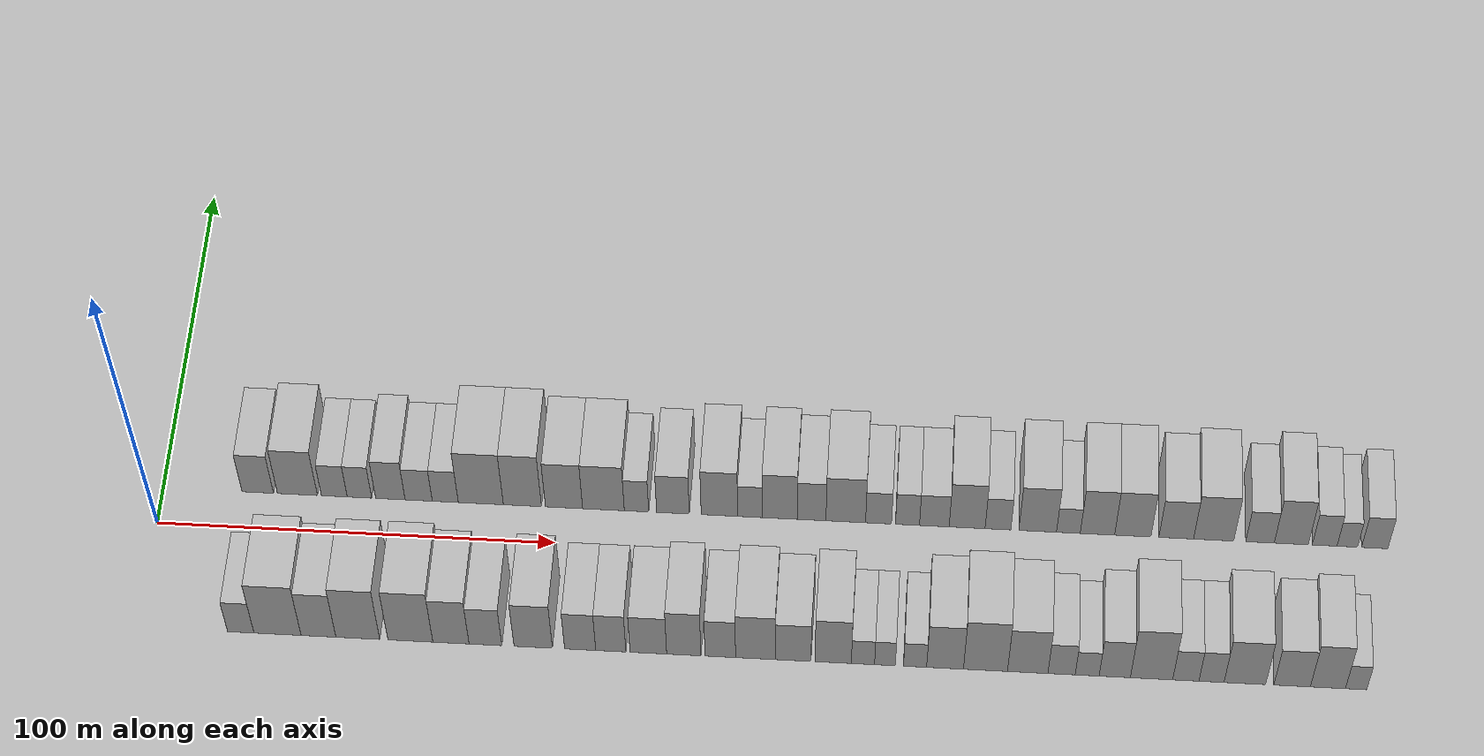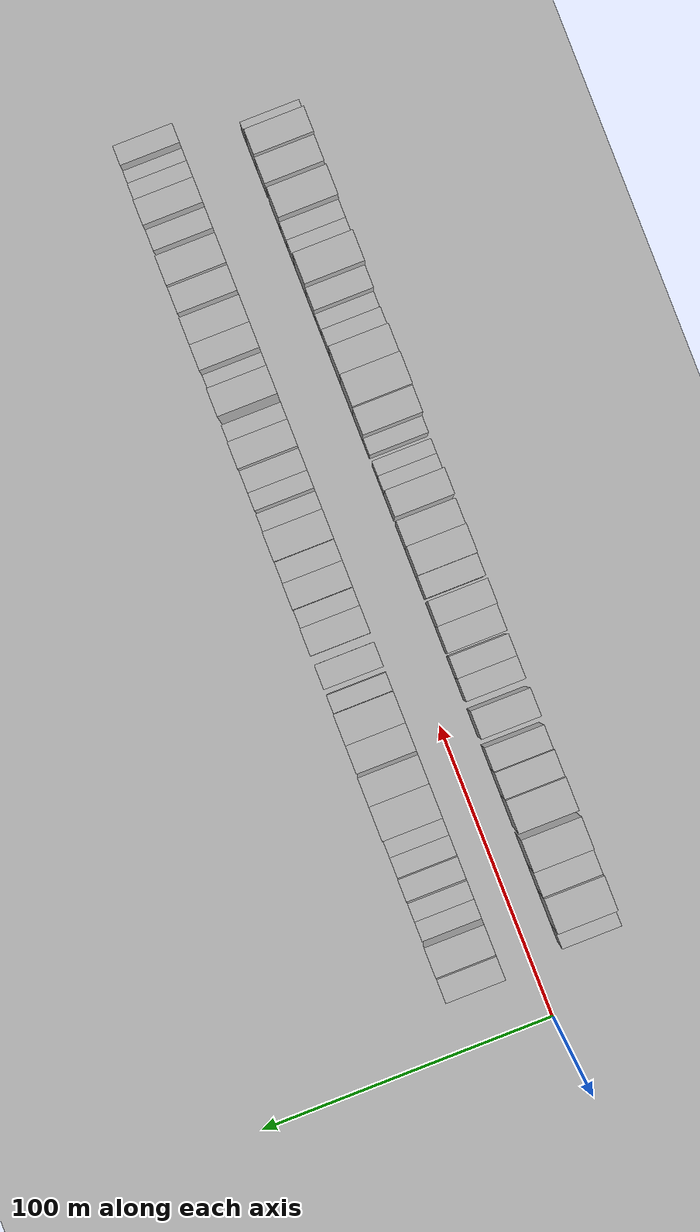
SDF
<?xml version="1.0" encoding="utf-8"?>

<sdf version="1.6">

   <world name="default">

      <gui fullscreen="0">

         <camera name="user_camera">

            <pose>-15 0 4.57585 0 0 0</pose>

            <view_controller>orbit</view_controller>

         </camera>

      </gui>

      <scene>

         <sky>

           <clouds>

             <speed>12</speed>

           </clouds>

         </sky>

         <ambient>0.4 0.4 0.4 1</ambient>

         <background>0.7 0.7 0.7 1</background>

         <shadows>1</shadows>

      </scene>

      <gravity>0 0 -9.8066</gravity>

      <magnetic_field>6e-06 2.3e-05 -4.2e-05</magnetic_field>

      <physics default="0" name="default_physics" type="ode">

         <ode>

            <solver>

               <type>quick</type>

               <iters>10</iters>

               <sor>1.0</sor>

               <use_dynamic_moi_rescaling>0</use_dynamic_moi_rescaling>

            </solver>

            <constraints>

               <cfm>0</cfm>

               <erp>0.2</erp>

               <contact_max_correcting_vel>100</contact_max_correcting_vel>

               <contact_surface_layer>0.001</contact_surface_layer>

            </constraints>

         </ode>

         <max_step_size>0.004</max_step_size>

         <real_time_factor>1</real_time_factor>

         <real_time_update_rate>250</real_time_update_rate>

      </physics>

      <light name="sun" type="directional">

         <cast_shadows>1</cast_shadows>

         <pose>0 0 10 0 0 0</pose>

         <diffuse>0.8 0.8 0.8 1</diffuse>

         <specular>0.2 0.2 0.2 1</specular>

         <attenuation>

            <range>1000</range>

            <constant>0.9</constant>

            <linear>0.01</linear>

            <quadratic>0.001</quadratic>

         </attenuation>

         <direction>-0.5 0.1 -0.9</direction>

      </light>

      <include>

         <name>ground_plane_1</name>

         <uri>model://HANNAS_ground_plane</uri>

         <pose>0 0 0  0 0 0</pose>

      </include>

      <include>

         <name>ground_plane_2</name>

         <uri>model://HANNAS_ground_plane</uri>

         <pose>100 0 0  0 0 0</pose>

      </include>

      <model name="building_1">

         <static>1</static>

         <pose frame="">23.9782 20.0000 0 0.000000 0.000000 1.570796</pose>

         <link name="link">

            <pose frame="">0 0 9.00 0 0 0</pose>

            <collision name="collision">

               <geometry>

                  <box>

                     <size>20.0000 7.9564 18.0000</size>

                  </box>

               </geometry>

               <max_contacts>10</max_contacts>

               <surface>

                  <contact>

                     <ode/>

                  </contact>

                  <bounce/>

                  <friction>

                     <torsional>

                        <ode/>

                     </torsional>

                     <ode/>

                  </friction>

               </surface>

            </collision>

            <visual name="visual">

               <cast_shadows>0</cast_shadows>

               <geometry>

                  <box>

                     <size>20.0000 7.9564 18.0000</size>

                  </box>

               </geometry>

               <material>

                  <script>

                     <uri>model://HANNAS_wall/materials/scripts</uri>

                     <uri>model://HANNAS_wall/materials/textures</uri>

                     <name>vrc/HANNAS_wall</name>

                  </script>

               </material>

            </visual>

            <self_collide>0</self_collide>

            <enable_wind>0</enable_wind>

            <kinematic>0</kinematic>

         </link>

      </model>

      <model name="building_2">

         <static>1</static>

         <pose frame="">34.0243 20.0000 0 0.000000 0.000000 1.570796</pose>

         <link name="link">

            <pose frame="">0 0 10.50 0 0 0</pose>

            <collision name="collision">

               <geometry>

                  <box>

                     <size>20.0000 10.1359 21.0000</size>

                  </box>

               </geometry>

               <max_contacts>10</max_contacts>

               <surface>

                  <contact>

                     <ode/>

                  </contact>

                  <bounce/>

                  <friction>

                     <torsional>

                        <ode/>

                     </torsional>

                     <ode/>

                  </friction>

               </surface>

            </collision>

            <visual name="visual">

               <cast_shadows>0</cast_shadows>

               <geometry>

                  <box>

                     <size>20.0000 10.1359 21.0000</size>

                  </box>

               </geometry>

               <material>

                  <script>

                     <uri>model://HANNAS_wall/materials/scripts</uri>

                     <uri>model://HANNAS_wall/materials/textures</uri>

                     <name>vrc/HANNAS_wall</name>

                  </script>

               </material>

            </visual>

            <self_collide>0</self_collide>

            <enable_wind>0</enable_wind>

            <kinematic>0</kinematic>

         </link>

      </model>

      <model name="building_3">

         <static>1</static>

         <pose frame="">43.3520 20.0000 0 0.000000 0.000000 1.570796</pose>

         <link name="link">

            <pose frame="">0 0 7.50 0 0 0</pose>

            <collision name="collision">

               <geometry>

                  <box>

                     <size>20.0000 6.5194 15.0000</size>

                  </box>

               </geometry>

               <max_contacts>10</max_contacts>

               <surface>

                  <contact>

                     <ode/>

                  </contact>

                  <bounce/>

                  <friction>

                     <torsional>

                        <ode/>

                     </torsional>

                     <ode/>

                  </friction>

               </surface>

            </collision>

            <visual name="visual">

               <cast_shadows>0</cast_shadows>

               <geometry>

                  <box>

                     <size>20.0000 6.5194 15.0000</size>

                  </box>

               </geometry>

               <material>

                  <script>

                     <uri>model://HANNAS_wall/materials/scripts</uri>

                     <uri>model://HANNAS_wall/materials/textures</uri>

                     <name>vrc/HANNAS_wall</name>

                  </script>

               </material>

            </visual>

            <self_collide>0</self_collide>

            <enable_wind>0</enable_wind>

            <kinematic>0</kinematic>

         </link>

      </model>

      <model name="building_4">

         <static>1</static>

         <pose frame="">49.7134 20.0000 0 0.000000 0.000000 1.570796</pose>

         <link name="link">

            <pose frame="">0 0 7.50 0 0 0</pose>

            <collision name="collision">

               <geometry>

                  <box>

                     <size>20.0000 6.2034 15.0000</size>

                  </box>

               </geometry>

               <max_contacts>10</max_contacts>

               <surface>

                  <contact>

                     <ode/>

                  </contact>

                  <bounce/>

                  <friction>

                     <torsional>

                        <ode/>

                     </torsional>

                     <ode/>

                  </friction>

               </surface>

            </collision>

            <visual name="visual">

               <cast_shadows>0</cast_shadows>

               <geometry>

                  <box>

                     <size>20.0000 6.2034 15.0000</size>

                  </box>

               </geometry>

               <material>

                  <script>

                     <uri>model://HANNAS_wall/materials/scripts</uri>

                     <uri>model://HANNAS_wall/materials/textures</uri>

                     <name>vrc/HANNAS_wall</name>

                  </script>

               </material>

            </visual>

            <self_collide>0</self_collide>

            <enable_wind>0</enable_wind>

            <kinematic>0</kinematic>

         </link>

      </model>

      <model name="building_5">

         <static>1</static>

         <pose frame="">57.5390 20.0000 0 0.000000 0.000000 1.570796</pose>

         <link name="link">

            <pose frame="">0 0 9.00 0 0 0</pose>

            <collision name="collision">

               <geometry>

                  <box>

                     <size>20.0000 7.4479 18.0000</size>

                  </box>

               </geometry>

               <max_contacts>10</max_contacts>

               <surface>

                  <contact>

                     <ode/>

                  </contact>

                  <bounce/>

                  <friction>

                     <torsional>

                        <ode/>

                     </torsional>

                     <ode/>

                  </friction>

               </surface>

            </collision>

            <visual name="visual">

               <cast_shadows>0</cast_shadows>

               <geometry>

                  <box>

                     <size>20.0000 7.4479 18.0000</size>

                  </box>

               </geometry>

               <material>

                  <script>

                     <uri>model://HANNAS_wall/materials/scripts</uri>

                     <uri>model://HANNAS_wall/materials/textures</uri>

                     <name>vrc/HANNAS_wall</name>

                  </script>

               </material>

            </visual>

            <self_collide>0</self_collide>

            <enable_wind>0</enable_wind>

            <kinematic>0</kinematic>

         </link>

      </model>

      <model name="building_6">

         <static>1</static>

         <pose frame="">64.6937 20.0000 0 0.000000 0.000000 1.570796</pose>

         <link name="link">

            <pose frame="">0 0 7.50 0 0 0</pose>

            <collision name="collision">

               <geometry>

                  <box>

                     <size>20.0000 6.8614 15.0000</size>

                  </box>

               </geometry>

               <max_contacts>10</max_contacts>

               <surface>

                  <contact>

                     <ode/>

                  </contact>

                  <bounce/>

                  <friction>

                     <torsional>

                        <ode/>

                     </torsional>

                     <ode/>

                  </friction>

               </surface>

            </collision>

            <visual name="visual">

               <cast_shadows>0</cast_shadows>

               <geometry>

                  <box>

                     <size>20.0000 6.8614 15.0000</size>

                  </box>

               </geometry>

               <material>

                  <script>

                     <uri>model://HANNAS_wall/materials/scripts</uri>

                     <uri>model://HANNAS_wall/materials/textures</uri>

                     <name>vrc/HANNAS_wall</name>

                  </script>

               </material>

            </visual>

            <self_collide>0</self_collide>

            <enable_wind>0</enable_wind>

            <kinematic>0</kinematic>

         </link>

      </model>

      <model name="building_7">

         <static>1</static>

         <pose frame="">71.4064 20.0000 0 0.000000 0.000000 1.570796</pose>

         <link name="link">

            <pose frame="">0 0 7.50 0 0 0</pose>

            <collision name="collision">

               <geometry>

                  <box>

                     <size>20.0000 6.5641 15.0000</size>

                  </box>

               </geometry>

               <max_contacts>10</max_contacts>

               <surface>

                  <contact>

                     <ode/>

                  </contact>

                  <bounce/>

                  <friction>

                     <torsional>

                        <ode/>

                     </torsional>

                     <ode/>

                  </friction>

               </surface>

            </collision>

            <visual name="visual">

               <cast_shadows>0</cast_shadows>

               <geometry>

                  <box>

                     <size>20.0000 6.5641 15.0000</size>

                  </box>

               </geometry>

               <material>

                  <script>

                     <uri>model://HANNAS_wall/materials/scripts</uri>

                     <uri>model://HANNAS_wall/materials/textures</uri>

                     <name>vrc/HANNAS_wall</name>

                  </script>

               </material>

            </visual>

            <self_collide>0</self_collide>

            <enable_wind>0</enable_wind>

            <kinematic>0</kinematic>

         </link>

      </model>

      <model name="building_8">

         <static>1</static>

         <pose frame="">80.3810 20.0000 0 0.000000 0.000000 1.570796</pose>

         <link name="link">

            <pose frame="">0 0 12.00 0 0 0</pose>

            <collision name="collision">

               <geometry>

                  <box>

                     <size>20.0000 11.3850 24.0000</size>

                  </box>

               </geometry>

               <max_contacts>10</max_contacts>

               <surface>

                  <contact>

                     <ode/>

                  </contact>

                  <bounce/>

                  <friction>

                     <torsional>

                        <ode/>

                     </torsional>

                     <ode/>

                  </friction>

               </surface>

            </collision>

            <visual name="visual">

               <cast_shadows>0</cast_shadows>

               <geometry>

                  <box>

                     <size>20.0000 11.3850 24.0000</size>

                  </box>

               </geometry>

               <material>

                  <script>

                     <uri>model://HANNAS_wall/materials/scripts</uri>

                     <uri>model://HANNAS_wall/materials/textures</uri>

                     <name>vrc/HANNAS_wall</name>

                  </script>

               </material>

            </visual>

            <self_collide>0</self_collide>

            <enable_wind>0</enable_wind>

            <kinematic>0</kinematic>

         </link>

      </model>

      <model name="building_9">

         <static>1</static>

         <pose frame="">90.8834 20.0000 0 0.000000 0.000000 1.570796</pose>

         <link name="link">

            <pose frame="">0 0 12.00 0 0 0</pose>

            <collision name="collision">

               <geometry>

                  <box>

                     <size>20.0000 9.6197 24.0000</size>

                  </box>

               </geometry>

               <max_contacts>10</max_contacts>

               <surface>

                  <contact>

                     <ode/>

                  </contact>

                  <bounce/>

                  <friction>

                     <torsional>

                        <ode/>

                     </torsional>

                     <ode/>

                  </friction>

               </surface>

            </collision>

            <visual name="visual">

               <cast_shadows>0</cast_shadows>

               <geometry>

                  <box>

                     <size>20.0000 9.6197 24.0000</size>

                  </box>

               </geometry>

               <material>

                  <script>

                     <uri>model://HANNAS_wall/materials/scripts</uri>

                     <uri>model://HANNAS_wall/materials/textures</uri>

                     <name>vrc/HANNAS_wall</name>

                  </script>

               </material>

            </visual>

            <self_collide>0</self_collide>

            <enable_wind>0</enable_wind>

            <kinematic>0</kinematic>

         </link>

      </model>

      <model name="building_10">

         <static>1</static>

         <pose frame="">101.3758 20.0000 0 0.000000 0.000000 1.570796</pose>

         <link name="link">

            <pose frame="">0 0 10.50 0 0 0</pose>

            <collision name="collision">

               <geometry>

                  <box>

                     <size>20.0000 9.3652 21.0000</size>

                  </box>

               </geometry>

               <max_contacts>10</max_contacts>

               <surface>

                  <contact>

                     <ode/>

                  </contact>

                  <bounce/>

                  <friction>

                     <torsional>

                        <ode/>

                     </torsional>

                     <ode/>

                  </friction>

               </surface>

            </collision>

            <visual name="visual">

               <cast_shadows>0</cast_shadows>

               <geometry>

                  <box>

                     <size>20.0000 9.3652 21.0000</size>

                  </box>

               </geometry>

               <material>

                  <script>

                     <uri>model://HANNAS_wall/materials/scripts</uri>

                     <uri>model://HANNAS_wall/materials/textures</uri>

                     <name>vrc/HANNAS_wall</name>

                  </script>

               </material>

            </visual>

            <self_collide>0</self_collide>

            <enable_wind>0</enable_wind>

            <kinematic>0</kinematic>

         </link>

      </model>

      <model name="building_11">

         <static>1</static>

         <pose frame="">111.3065 20.0000 0 0.000000 0.000000 1.570796</pose>

         <link name="link">

            <pose frame="">0 0 10.50 0 0 0</pose>

            <collision name="collision">

               <geometry>

                  <box>

                     <size>20.0000 10.4962 21.0000</size>

                  </box>

               </geometry>

               <max_contacts>10</max_contacts>

               <surface>

                  <contact>

                     <ode/>

                  </contact>

                  <bounce/>

                  <friction>

                     <torsional>

                        <ode/>

                     </torsional>

                     <ode/>

                  </friction>

               </surface>

            </collision>

            <visual name="visual">

               <cast_shadows>0</cast_shadows>

               <geometry>

                  <box>

                     <size>20.0000 10.4962 21.0000</size>

                  </box>

               </geometry>

               <material>

                  <script>

                     <uri>model://HANNAS_wall/materials/scripts</uri>

                     <uri>model://HANNAS_wall/materials/textures</uri>

                     <name>vrc/HANNAS_wall</name>

                  </script>

               </material>

            </visual>

            <self_collide>0</self_collide>

            <enable_wind>0</enable_wind>

            <kinematic>0</kinematic>

         </link>

      </model>

      <model name="building_12">

         <static>1</static>

         <pose frame="">119.6241 20.0000 0 0.000000 0.000000 1.570796</pose>

         <link name="link">

            <pose frame="">0 0 7.50 0 0 0</pose>

            <collision name="collision">

               <geometry>

                  <box>

                     <size>20.0000 6.1389 15.0000</size>

                  </box>

               </geometry>

               <max_contacts>10</max_contacts>

               <surface>

                  <contact>

                     <ode/>

                  </contact>

                  <bounce/>

                  <friction>

                     <torsional>

                        <ode/>

                     </torsional>

                     <ode/>

                  </friction>

               </surface>

            </collision>

            <visual name="visual">

               <cast_shadows>0</cast_shadows>

               <geometry>

                  <box>

                     <size>20.0000 6.1389 15.0000</size>

                  </box>

               </geometry>

               <material>

                  <script>

                     <uri>model://HANNAS_wall/materials/scripts</uri>

                     <uri>model://HANNAS_wall/materials/textures</uri>

                     <name>vrc/HANNAS_wall</name>

                  </script>

               </material>

            </visual>

            <self_collide>0</self_collide>

            <enable_wind>0</enable_wind>

            <kinematic>0</kinematic>

         </link>

      </model>

      <model name="building_13">

         <static>1</static>

         <pose frame="">128.7997 20.0000 0 0.000000 0.000000 1.570796</pose>

         <link name="link">

            <pose frame="">0 0 9.00 0 0 0</pose>

            <collision name="collision">

               <geometry>

                  <box>

                     <size>20.0000 8.2124 18.0000</size>

                  </box>

               </geometry>

               <max_contacts>10</max_contacts>

               <surface>

                  <contact>

                     <ode/>

                  </contact>

                  <bounce/>

                  <friction>

                     <torsional>

                        <ode/>

                     </torsional>

                     <ode/>

                  </friction>

               </surface>

            </collision>

            <visual name="visual">

               <cast_shadows>0</cast_shadows>

               <geometry>

                  <box>

                     <size>20.0000 8.2124 18.0000</size>

                  </box>

               </geometry>

               <material>

                  <script>

                     <uri>model://HANNAS_wall/materials/scripts</uri>

                     <uri>model://HANNAS_wall/materials/textures</uri>

                     <name>vrc/HANNAS_wall</name>

                  </script>

               </material>

            </visual>

            <self_collide>0</self_collide>

            <enable_wind>0</enable_wind>

            <kinematic>0</kinematic>

         </link>

      </model>

      <model name="building_14">

         <static>1</static>

         <pose frame="">140.4853 20.0000 0 0.000000 0.000000 1.570796</pose>

         <link name="link">

            <pose frame="">0 0 10.50 0 0 0</pose>

            <collision name="collision">

               <geometry>

                  <box>

                     <size>20.0000 9.1588 21.0000</size>

                  </box>

               </geometry>

               <max_contacts>10</max_contacts>

               <surface>

                  <contact>

                     <ode/>

                  </contact>

                  <bounce/>

                  <friction>

                     <torsional>

                        <ode/>

                     </torsional>

                     <ode/>

                  </friction>

               </surface>

            </collision>

            <visual name="visual">

               <cast_shadows>0</cast_shadows>

               <geometry>

                  <box>

                     <size>20.0000 9.1588 21.0000</size>

                  </box>

               </geometry>

               <material>

                  <script>

                     <uri>model://HANNAS_wall/materials/scripts</uri>

                     <uri>model://HANNAS_wall/materials/textures</uri>

                     <name>vrc/HANNAS_wall</name>

                  </script>

               </material>

            </visual>

            <self_collide>0</self_collide>

            <enable_wind>0</enable_wind>

            <kinematic>0</kinematic>

         </link>

      </model>

      <model name="building_15">

         <static>1</static>

         <pose frame="">148.1402 20.0000 0 0.000000 0.000000 1.570796</pose>

         <link name="link">

            <pose frame="">0 0 7.50 0 0 0</pose>

            <collision name="collision">

               <geometry>

                  <box>

                     <size>20.0000 6.1510 15.0000</size>

                  </box>

               </geometry>

               <max_contacts>10</max_contacts>

               <surface>

                  <contact>

                     <ode/>

                  </contact>

                  <bounce/>

                  <friction>

                     <torsional>

                        <ode/>

                     </torsional>

                     <ode/>

                  </friction>

               </surface>

            </collision>

            <visual name="visual">

               <cast_shadows>0</cast_shadows>

               <geometry>

                  <box>

                     <size>20.0000 6.1510 15.0000</size>

                  </box>

               </geometry>

               <material>

                  <script>

                     <uri>model://HANNAS_wall/materials/scripts</uri>

                     <uri>model://HANNAS_wall/materials/textures</uri>

                     <name>vrc/HANNAS_wall</name>

                  </script>

               </material>

            </visual>

            <self_collide>0</self_collide>

            <enable_wind>0</enable_wind>

            <kinematic>0</kinematic>

         </link>

      </model>

      <model name="building_16">

         <static>1</static>

         <pose frame="">155.6129 20.0000 0 0.000000 0.000000 1.570796</pose>

         <link name="link">

            <pose frame="">0 0 10.50 0 0 0</pose>

            <collision name="collision">

               <geometry>

                  <box>

                     <size>20.0000 8.7945 21.0000</size>

                  </box>

               </geometry>

               <max_contacts>10</max_contacts>

               <surface>

                  <contact>

                     <ode/>

                  </contact>

                  <bounce/>

                  <friction>

                     <torsional>

                        <ode/>

                     </torsional>

                     <ode/>

                  </friction>

               </surface>

            </collision>

            <visual name="visual">

               <cast_shadows>0</cast_shadows>

               <geometry>

                  <box>

                     <size>20.0000 8.7945 21.0000</size>

                  </box>

               </geometry>

               <material>

                  <script>

                     <uri>model://HANNAS_wall/materials/scripts</uri>

                     <uri>model://HANNAS_wall/materials/textures</uri>

                     <name>vrc/HANNAS_wall</name>

                  </script>

               </material>

            </visual>

            <self_collide>0</self_collide>

            <enable_wind>0</enable_wind>

            <kinematic>0</kinematic>

         </link>

      </model>

      <model name="building_17">

         <static>1</static>

         <pose frame="">163.6215 20.0000 0 0.000000 0.000000 1.570796</pose>

         <link name="link">

            <pose frame="">0 0 9.00 0 0 0</pose>

            <collision name="collision">

               <geometry>

                  <box>

                     <size>20.0000 7.2226 18.0000</size>

                  </box>

               </geometry>

               <max_contacts>10</max_contacts>

               <surface>

                  <contact>

                     <ode/>

                  </contact>

                  <bounce/>

                  <friction>

                     <torsional>

                        <ode/>

                     </torsional>

                     <ode/>

                  </friction>

               </surface>

            </collision>

            <visual name="visual">

               <cast_shadows>0</cast_shadows>

               <geometry>

                  <box>

                     <size>20.0000 7.2226 18.0000</size>

                  </box>

               </geometry>

               <material>

                  <script>

                     <uri>model://HANNAS_wall/materials/scripts</uri>

                     <uri>model://HANNAS_wall/materials/textures</uri>

                     <name>vrc/HANNAS_wall</name>

                  </script>

               </material>

            </visual>

            <self_collide>0</self_collide>

            <enable_wind>0</enable_wind>

            <kinematic>0</kinematic>

         </link>

      </model>

      <model name="building_18">

         <static>1</static>

         <pose frame="">172.2004 20.0000 0 0.000000 0.000000 1.570796</pose>

         <link name="link">

            <pose frame="">0 0 10.50 0 0 0</pose>

            <collision name="collision">

               <geometry>

                  <box>

                     <size>20.0000 9.9352 21.0000</size>

                  </box>

               </geometry>

               <max_contacts>10</max_contacts>

               <surface>

                  <contact>

                     <ode/>

                  </contact>

                  <bounce/>

                  <friction>

                     <torsional>

                        <ode/>

                     </torsional>

                     <ode/>

                  </friction>

               </surface>

            </collision>

            <visual name="visual">

               <cast_shadows>0</cast_shadows>

               <geometry>

                  <box>

                     <size>20.0000 9.9352 21.0000</size>

                  </box>

               </geometry>

               <material>

                  <script>

                     <uri>model://HANNAS_wall/materials/scripts</uri>

                     <uri>model://HANNAS_wall/materials/textures</uri>

                     <name>vrc/HANNAS_wall</name>

                  </script>

               </material>

            </visual>

            <self_collide>0</self_collide>

            <enable_wind>0</enable_wind>

            <kinematic>0</kinematic>

         </link>

      </model>

      <model name="building_19">

         <static>1</static>

         <pose frame="">180.4154 20.0000 0 0.000000 0.000000 1.570796</pose>

         <link name="link">

            <pose frame="">0 0 7.50 0 0 0</pose>

            <collision name="collision">

               <geometry>

                  <box>

                     <size>20.0000 6.4949 15.0000</size>

                  </box>

               </geometry>

               <max_contacts>10</max_contacts>

               <surface>

                  <contact>

                     <ode/>

                  </contact>

                  <bounce/>

                  <friction>

                     <torsional>

                        <ode/>

                     </torsional>

                     <ode/>

                  </friction>

               </surface>

            </collision>

            <visual name="visual">

               <cast_shadows>0</cast_shadows>

               <geometry>

                  <box>

                     <size>20.0000 6.4949 15.0000</size>

                  </box>

               </geometry>

               <material>

                  <script>

                     <uri>model://HANNAS_wall/materials/scripts</uri>

                     <uri>model://HANNAS_wall/materials/textures</uri>

                     <name>vrc/HANNAS_wall</name>

                  </script>

               </material>

            </visual>

            <self_collide>0</self_collide>

            <enable_wind>0</enable_wind>

            <kinematic>0</kinematic>

         </link>

      </model>

      <model name="building_20">

         <static>1</static>

         <pose frame="">187.6658 20.0000 0 0.000000 0.000000 1.570796</pose>

         <link name="link">

            <pose frame="">0 0 7.50 0 0 0</pose>

            <collision name="collision">

               <geometry>

                  <box>

                     <size>20.0000 6.0058 15.0000</size>

                  </box>

               </geometry>

               <max_contacts>10</max_contacts>

               <surface>

                  <contact>

                     <ode/>

                  </contact>

                  <bounce/>

                  <friction>

                     <torsional>

                        <ode/>

                     </torsional>

                     <ode/>

                  </friction>

               </surface>

            </collision>

            <visual name="visual">

               <cast_shadows>0</cast_shadows>

               <geometry>

                  <box>

                     <size>20.0000 6.0058 15.0000</size>

                  </box>

               </geometry>

               <material>

                  <script>

                     <uri>model://HANNAS_wall/materials/scripts</uri>

                     <uri>model://HANNAS_wall/materials/textures</uri>

                     <name>vrc/HANNAS_wall</name>

                  </script>

               </material>

            </visual>

            <self_collide>0</self_collide>

            <enable_wind>0</enable_wind>

            <kinematic>0</kinematic>

         </link>

      </model>

      <model name="building_21">

         <static>1</static>

         <pose frame="">194.3858 20.0000 0 0.000000 0.000000 1.570796</pose>

         <link name="link">

            <pose frame="">0 0 7.50 0 0 0</pose>

            <collision name="collision">

               <geometry>

                  <box>

                     <size>20.0000 7.4343 15.0000</size>

                  </box>

               </geometry>

               <max_contacts>10</max_contacts>

               <surface>

                  <contact>

                     <ode/>

                  </contact>

                  <bounce/>

                  <friction>

                     <torsional>

                        <ode/>

                     </torsional>

                     <ode/>

                  </friction>

               </surface>

            </collision>

            <visual name="visual">

               <cast_shadows>0</cast_shadows>

               <geometry>

                  <box>

                     <size>20.0000 7.4343 15.0000</size>

                  </box>

               </geometry>

               <material>

                  <script>

                     <uri>model://HANNAS_wall/materials/scripts</uri>

                     <uri>model://HANNAS_wall/materials/textures</uri>

                     <name>vrc/HANNAS_wall</name>

                  </script>

               </material>

            </visual>

            <self_collide>0</self_collide>

            <enable_wind>0</enable_wind>

            <kinematic>0</kinematic>

         </link>

      </model>

      <model name="building_22">

         <static>1</static>

         <pose frame="">202.5969 20.0000 0 0.000000 0.000000 1.570796</pose>

         <link name="link">

            <pose frame="">0 0 10.50 0 0 0</pose>

            <collision name="collision">

               <geometry>

                  <box>

                     <size>20.0000 8.9879 21.0000</size>

                  </box>

               </geometry>

               <max_contacts>10</max_contacts>

               <surface>

                  <contact>

                     <ode/>

                  </contact>

                  <bounce/>

                  <friction>

                     <torsional>

                        <ode/>

                     </torsional>

                     <ode/>

                  </friction>

               </surface>

            </collision>

            <visual name="visual">

               <cast_shadows>0</cast_shadows>

               <geometry>

                  <box>

                     <size>20.0000 8.9879 21.0000</size>

                  </box>

               </geometry>

               <material>

                  <script>

                     <uri>model://HANNAS_wall/materials/scripts</uri>

                     <uri>model://HANNAS_wall/materials/textures</uri>

                     <name>vrc/HANNAS_wall</name>

                  </script>

               </material>

            </visual>

            <self_collide>0</self_collide>

            <enable_wind>0</enable_wind>

            <kinematic>0</kinematic>

         </link>

      </model>

      <model name="building_23">

         <static>1</static>

         <pose frame="">210.3130 20.0000 0 0.000000 0.000000 1.570796</pose>

         <link name="link">

            <pose frame="">0 0 7.50 0 0 0</pose>

            <collision name="collision">

               <geometry>

                  <box>

                     <size>20.0000 6.4444 15.0000</size>

                  </box>

               </geometry>

               <max_contacts>10</max_contacts>

               <surface>

                  <contact>

                     <ode/>

                  </contact>

                  <bounce/>

                  <friction>

                     <torsional>

                        <ode/>

                     </torsional>

                     <ode/>

                  </friction>

               </surface>

            </collision>

            <visual name="visual">

               <cast_shadows>0</cast_shadows>

               <geometry>

                  <box>

                     <size>20.0000 6.4444 15.0000</size>

                  </box>

               </geometry>

               <material>

                  <script>

                     <uri>model://HANNAS_wall/materials/scripts</uri>

                     <uri>model://HANNAS_wall/materials/textures</uri>

                     <name>vrc/HANNAS_wall</name>

                  </script>

               </material>

            </visual>

            <self_collide>0</self_collide>

            <enable_wind>0</enable_wind>

            <kinematic>0</kinematic>

         </link>

      </model>

      <model name="building_24">

         <static>1</static>

         <pose frame="">220.2439 20.0000 0 0.000000 0.000000 1.570796</pose>

         <link name="link">

            <pose frame="">0 0 10.50 0 0 0</pose>

            <collision name="collision">

               <geometry>

                  <box>

                     <size>20.0000 9.4174 21.0000</size>

                  </box>

               </geometry>

               <max_contacts>10</max_contacts>

               <surface>

                  <contact>

                     <ode/>

                  </contact>

                  <bounce/>

                  <friction>

                     <torsional>

                        <ode/>

                     </torsional>

                     <ode/>

                  </friction>

               </surface>

            </collision>

            <visual name="visual">

               <cast_shadows>0</cast_shadows>

               <geometry>

                  <box>

                     <size>20.0000 9.4174 21.0000</size>

                  </box>

               </geometry>

               <material>

                  <script>

                     <uri>model://HANNAS_wall/materials/scripts</uri>

                     <uri>model://HANNAS_wall/materials/textures</uri>

                     <name>vrc/HANNAS_wall</name>

                  </script>

               </material>

            </visual>

            <self_collide>0</self_collide>

            <enable_wind>0</enable_wind>

            <kinematic>0</kinematic>

         </link>

      </model>

      <model name="building_25">

         <static>1</static>

         <pose frame="">227.9159 20.0000 0 0.000000 0.000000 1.570796</pose>

         <link name="link">

            <pose frame="">0 0 6.00 0 0 0</pose>

            <collision name="collision">

               <geometry>

                  <box>

                     <size>20.0000 5.9267 12.0000</size>

                  </box>

               </geometry>

               <max_contacts>10</max_contacts>

               <surface>

                  <contact>

                     <ode/>

                  </contact>

                  <bounce/>

                  <friction>

                     <torsional>

                        <ode/>

                     </torsional>

                     <ode/>

                  </friction>

               </surface>

            </collision>

            <visual name="visual">

               <cast_shadows>0</cast_shadows>

               <geometry>

                  <box>

                     <size>20.0000 5.9267 12.0000</size>

                  </box>

               </geometry>

               <material>

                  <script>

                     <uri>model://HANNAS_wall/materials/scripts</uri>

                     <uri>model://HANNAS_wall/materials/textures</uri>

                     <name>vrc/HANNAS_wall</name>

                  </script>

               </material>

            </visual>

            <self_collide>0</self_collide>

            <enable_wind>0</enable_wind>

            <kinematic>0</kinematic>

         </link>

      </model>

      <model name="building_26">

         <static>1</static>

         <pose frame="">235.1707 20.0000 0 0.000000 0.000000 1.570796</pose>

         <link name="link">

            <pose frame="">0 0 10.50 0 0 0</pose>

            <collision name="collision">

               <geometry>

                  <box>

                     <size>20.0000 8.5828 21.0000</size>

                  </box>

               </geometry>

               <max_contacts>10</max_contacts>

               <surface>

                  <contact>

                     <ode/>

                  </contact>

                  <bounce/>

                  <friction>

                     <torsional>

                        <ode/>

                     </torsional>

                     <ode/>

                  </friction>

               </surface>

            </collision>

            <visual name="visual">

               <cast_shadows>0</cast_shadows>

               <geometry>

                  <box>

                     <size>20.0000 8.5828 21.0000</size>

                  </box>

               </geometry>

               <material>

                  <script>

                     <uri>model://HANNAS_wall/materials/scripts</uri>

                     <uri>model://HANNAS_wall/materials/textures</uri>

                     <name>vrc/HANNAS_wall</name>

                  </script>

               </material>

            </visual>

            <self_collide>0</self_collide>

            <enable_wind>0</enable_wind>

            <kinematic>0</kinematic>

         </link>

      </model>

      <model name="building_27">

         <static>1</static>

         <pose frame="">243.9886 20.0000 0 0.000000 0.000000 1.570796</pose>

         <link name="link">

            <pose frame="">0 0 10.50 0 0 0</pose>

            <collision name="collision">

               <geometry>

                  <box>

                     <size>20.0000 9.0531 21.0000</size>

                  </box>

               </geometry>

               <max_contacts>10</max_contacts>

               <surface>

                  <contact>

                     <ode/>

                  </contact>

                  <bounce/>

                  <friction>

                     <torsional>

                        <ode/>

                     </torsional>

                     <ode/>

                  </friction>

               </surface>

            </collision>

            <visual name="visual">

               <cast_shadows>0</cast_shadows>

               <geometry>

                  <box>

                     <size>20.0000 9.0531 21.0000</size>

                  </box>

               </geometry>

               <material>

                  <script>

                     <uri>model://HANNAS_wall/materials/scripts</uri>

                     <uri>model://HANNAS_wall/materials/textures</uri>

                     <name>vrc/HANNAS_wall</name>

                  </script>

               </material>

            </visual>

            <self_collide>0</self_collide>

            <enable_wind>0</enable_wind>

            <kinematic>0</kinematic>

         </link>

      </model>

      <model name="building_28">

         <static>1</static>

         <pose frame="">254.8428 20.0000 0 0.000000 0.000000 1.570796</pose>

         <link name="link">

            <pose frame="">0 0 9.00 0 0 0</pose>

            <collision name="collision">

               <geometry>

                  <box>

                     <size>20.0000 8.6553 18.0000</size>

                  </box>

               </geometry>

               <max_contacts>10</max_contacts>

               <surface>

                  <contact>

                     <ode/>

                  </contact>

                  <bounce/>

                  <friction>

                     <torsional>

                        <ode/>

                     </torsional>

                     <ode/>

                  </friction>

               </surface>

            </collision>

            <visual name="visual">

               <cast_shadows>0</cast_shadows>

               <geometry>

                  <box>

                     <size>20.0000 8.6553 18.0000</size>

                  </box>

               </geometry>

               <material>

                  <script>

                     <uri>model://HANNAS_wall/materials/scripts</uri>

                     <uri>model://HANNAS_wall/materials/textures</uri>

                     <name>vrc/HANNAS_wall</name>

                  </script>

               </material>

            </visual>

            <self_collide>0</self_collide>

            <enable_wind>0</enable_wind>

            <kinematic>0</kinematic>

         </link>

      </model>

      <model name="building_29">

         <static>1</static>

         <pose frame="">264.1635 20.0000 0 0.000000 0.000000 1.570796</pose>

         <link name="link">

            <pose frame="">0 0 10.50 0 0 0</pose>

            <collision name="collision">

               <geometry>

                  <box>

                     <size>20.0000 9.9860 21.0000</size>

                  </box>

               </geometry>

               <max_contacts>10</max_contacts>

               <surface>

                  <contact>

                     <ode/>

                  </contact>

                  <bounce/>

                  <friction>

                     <torsional>

                        <ode/>

                     </torsional>

                     <ode/>

                  </friction>

               </surface>

            </collision>

            <visual name="visual">

               <cast_shadows>0</cast_shadows>

               <geometry>

                  <box>

                     <size>20.0000 9.9860 21.0000</size>

                  </box>

               </geometry>

               <material>

                  <script>

                     <uri>model://HANNAS_wall/materials/scripts</uri>

                     <uri>model://HANNAS_wall/materials/textures</uri>

                     <name>vrc/HANNAS_wall</name>

                  </script>

               </material>

            </visual>

            <self_collide>0</self_collide>

            <enable_wind>0</enable_wind>

            <kinematic>0</kinematic>

         </link>

      </model>

      <model name="building_30">

         <static>1</static>

         <pose frame="">275.7116 20.0000 0 0.000000 0.000000 1.570796</pose>

         <link name="link">

            <pose frame="">0 0 7.50 0 0 0</pose>

            <collision name="collision">

               <geometry>

                  <box>

                     <size>20.0000 7.1102 15.0000</size>

                  </box>

               </geometry>

               <max_contacts>10</max_contacts>

               <surface>

                  <contact>

                     <ode/>

                  </contact>

                  <bounce/>

                  <friction>

                     <torsional>

                        <ode/>

                     </torsional>

                     <ode/>

                  </friction>

               </surface>

            </collision>

            <visual name="visual">

               <cast_shadows>0</cast_shadows>

               <geometry>

                  <box>

                     <size>20.0000 7.1102 15.0000</size>

                  </box>

               </geometry>

               <material>

                  <script>

                     <uri>model://HANNAS_wall/materials/scripts</uri>

                     <uri>model://HANNAS_wall/materials/textures</uri>

                     <name>vrc/HANNAS_wall</name>

                  </script>

               </material>

            </visual>

            <self_collide>0</self_collide>

            <enable_wind>0</enable_wind>

            <kinematic>0</kinematic>

         </link>

      </model>

      <model name="building_31">

         <static>1</static>

         <pose frame="">283.4940 20.0000 0 0.000000 0.000000 1.570796</pose>

         <link name="link">

            <pose frame="">0 0 10.50 0 0 0</pose>

            <collision name="collision">

               <geometry>

                  <box>

                     <size>20.0000 8.4546 21.0000</size>

                  </box>

               </geometry>

               <max_contacts>10</max_contacts>

               <surface>

                  <contact>

                     <ode/>

                  </contact>

                  <bounce/>

                  <friction>

                     <torsional>

                        <ode/>

                     </torsional>

                     <ode/>

                  </friction>

               </surface>

            </collision>

            <visual name="visual">

               <cast_shadows>0</cast_shadows>

               <geometry>

                  <box>

                     <size>20.0000 8.4546 21.0000</size>

                  </box>

               </geometry>

               <material>

                  <script>

                     <uri>model://HANNAS_wall/materials/scripts</uri>

                     <uri>model://HANNAS_wall/materials/textures</uri>

                     <name>vrc/HANNAS_wall</name>

                  </script>

               </material>

            </visual>

            <self_collide>0</self_collide>

            <enable_wind>0</enable_wind>

            <kinematic>0</kinematic>

         </link>

      </model>

      <model name="building_32">

         <static>1</static>

         <pose frame="">291.8101 20.0000 0 0.000000 0.000000 1.570796</pose>

         <link name="link">

            <pose frame="">0 0 7.50 0 0 0</pose>

            <collision name="collision">

               <geometry>

                  <box>

                     <size>20.0000 6.1775 15.0000</size>

                  </box>

               </geometry>

               <max_contacts>10</max_contacts>

               <surface>

                  <contact>

                     <ode/>

                  </contact>

                  <bounce/>

                  <friction>

                     <torsional>

                        <ode/>

                     </torsional>

                     <ode/>

                  </friction>

               </surface>

            </collision>

            <visual name="visual">

               <cast_shadows>0</cast_shadows>

               <geometry>

                  <box>

                     <size>20.0000 6.1775 15.0000</size>

                  </box>

               </geometry>

               <material>

                  <script>

                     <uri>model://HANNAS_wall/materials/scripts</uri>

                     <uri>model://HANNAS_wall/materials/textures</uri>

                     <name>vrc/HANNAS_wall</name>

                  </script>

               </material>

            </visual>

            <self_collide>0</self_collide>

            <enable_wind>0</enable_wind>

            <kinematic>0</kinematic>

         </link>

      </model>

      <model name="building_33">

         <static>1</static>

         <pose frame="">297.4344 20.0000 0 0.000000 0.000000 1.570796</pose>

         <link name="link">

            <pose frame="">0 0 6.00 0 0 0</pose>

            <collision name="collision">

               <geometry>

                  <box>

                     <size>20.0000 5.0711 12.0000</size>

                  </box>

               </geometry>

               <max_contacts>10</max_contacts>

               <surface>

                  <contact>

                     <ode/>

                  </contact>

                  <bounce/>

                  <friction>

                     <torsional>

                        <ode/>

                     </torsional>

                     <ode/>

                  </friction>

               </surface>

            </collision>

            <visual name="visual">

               <cast_shadows>0</cast_shadows>

               <geometry>

                  <box>

                     <size>20.0000 5.0711 12.0000</size>

                  </box>

               </geometry>

               <material>

                  <script>

                     <uri>model://HANNAS_wall/materials/scripts</uri>

                     <uri>model://HANNAS_wall/materials/textures</uri>

                     <name>vrc/HANNAS_wall</name>

                  </script>

               </material>

            </visual>

            <self_collide>0</self_collide>

            <enable_wind>0</enable_wind>

            <kinematic>0</kinematic>

         </link>

      </model>

      <model name="building_34">

         <static>1</static>

         <pose frame="">304.2357 20.0000 0 0.000000 0.000000 1.570796</pose>

         <link name="link">

            <pose frame="">0 0 7.50 0 0 0</pose>

            <collision name="collision">

               <geometry>

                  <box>

                     <size>20.0000 6.5314 15.0000</size>

                  </box>

               </geometry>

               <max_contacts>10</max_contacts>

               <surface>

                  <contact>

                     <ode/>

                  </contact>

                  <bounce/>

                  <friction>

                     <torsional>

                        <ode/>

                     </torsional>

                     <ode/>

                  </friction>

               </surface>

            </collision>

            <visual name="visual">

               <cast_shadows>0</cast_shadows>

               <geometry>

                  <box>

                     <size>20.0000 6.5314 15.0000</size>

                  </box>

               </geometry>

               <material>

                  <script>

                     <uri>model://HANNAS_wall/materials/scripts</uri>

                     <uri>model://HANNAS_wall/materials/textures</uri>

                     <name>vrc/HANNAS_wall</name>

                  </script>

               </material>

            </visual>

            <self_collide>0</self_collide>

            <enable_wind>0</enable_wind>

            <kinematic>0</kinematic>

         </link>

      </model>

      <model name="building_35">

         <static>1</static>

         <pose frame="">25.2598 -20.0000 0 0.000000 0.000000 1.570796</pose>

         <link name="link">

            <pose frame="">0 0 7.50 0 0 0</pose>

            <collision name="collision">

               <geometry>

                  <box>

                     <size>20.0000 6.5197 15.0000</size>

                  </box>

               </geometry>

               <max_contacts>10</max_contacts>

               <surface>

                  <contact>

                     <ode/>

                  </contact>

                  <bounce/>

                  <friction>

                     <torsional>

                        <ode/>

                     </torsional>

                     <ode/>

                  </friction>

               </surface>

            </collision>

            <visual name="visual">

               <cast_shadows>0</cast_shadows>

               <geometry>

                  <box>

                     <size>20.0000 6.5197 15.0000</size>

                  </box>

               </geometry>

               <material>

                  <script>

                     <uri>model://HANNAS_wall/materials/scripts</uri>

                     <uri>model://HANNAS_wall/materials/textures</uri>

                     <name>vrc/HANNAS_wall</name>

                  </script>

               </material>

            </visual>

            <self_collide>0</self_collide>

            <enable_wind>0</enable_wind>

            <kinematic>0</kinematic>

         </link>

      </model>

      <model name="building_36">

         <static>1</static>

         <pose frame="">34.3475 -20.0000 0 0.000000 0.000000 1.570796</pose>

         <link name="link">

            <pose frame="">0 0 12.00 0 0 0</pose>

            <collision name="collision">

               <geometry>

                  <box>

                     <size>20.0000 11.6556 24.0000</size>

                  </box>

               </geometry>

               <max_contacts>10</max_contacts>

               <surface>

                  <contact>

                     <ode/>

                  </contact>

                  <bounce/>

                  <friction>

                     <torsional>

                        <ode/>

                     </torsional>

                     <ode/>

                  </friction>

               </surface>

            </collision>

            <visual name="visual">

               <cast_shadows>0</cast_shadows>

               <geometry>

                  <box>

                     <size>20.0000 11.6556 24.0000</size>

                  </box>

               </geometry>

               <material>

                  <script>

                     <uri>model://HANNAS_wall/materials/scripts</uri>

                     <uri>model://HANNAS_wall/materials/textures</uri>

                     <name>vrc/HANNAS_wall</name>

                  </script>

               </material>

            </visual>

            <self_collide>0</self_collide>

            <enable_wind>0</enable_wind>

            <kinematic>0</kinematic>

         </link>

      </model>

      <model name="building_37">

         <static>1</static>

         <pose frame="">44.4739 -20.0000 0 0.000000 0.000000 1.570796</pose>

         <link name="link">

            <pose frame="">0 0 10.50 0 0 0</pose>

            <collision name="collision">

               <geometry>

                  <box>

                     <size>20.0000 8.5973 21.0000</size>

                  </box>

               </geometry>

               <max_contacts>10</max_contacts>

               <surface>

                  <contact>

                     <ode/>

                  </contact>

                  <bounce/>

                  <friction>

                     <torsional>

                        <ode/>

                     </torsional>

                     <ode/>

                  </friction>

               </surface>

            </collision>

            <visual name="visual">

               <cast_shadows>0</cast_shadows>

               <geometry>

                  <box>

                     <size>20.0000 8.5973 21.0000</size>

                  </box>

               </geometry>

               <material>

                  <script>

                     <uri>model://HANNAS_wall/materials/scripts</uri>

                     <uri>model://HANNAS_wall/materials/textures</uri>

                     <name>vrc/HANNAS_wall</name>

                  </script>

               </material>

            </visual>

            <self_collide>0</self_collide>

            <enable_wind>0</enable_wind>

            <kinematic>0</kinematic>

         </link>

      </model>

      <model name="building_38">

         <static>1</static>

         <pose frame="">54.1903 -20.0000 0 0.000000 0.000000 1.570796</pose>

         <link name="link">

            <pose frame="">0 0 12.00 0 0 0</pose>

            <collision name="collision">

               <geometry>

                  <box>

                     <size>20.0000 10.8354 24.0000</size>

                  </box>

               </geometry>

               <max_contacts>10</max_contacts>

               <surface>

                  <contact>

                     <ode/>

                  </contact>

                  <bounce/>

                  <friction>

                     <torsional>

                        <ode/>

                     </torsional>

                     <ode/>

                  </friction>

               </surface>

            </collision>

            <visual name="visual">

               <cast_shadows>0</cast_shadows>

               <geometry>

                  <box>

                     <size>20.0000 10.8354 24.0000</size>

                  </box>

               </geometry>

               <material>

                  <script>

                     <uri>model://HANNAS_wall/materials/scripts</uri>

                     <uri>model://HANNAS_wall/materials/textures</uri>

                     <name>vrc/HANNAS_wall</name>

                  </script>

               </material>

            </visual>

            <self_collide>0</self_collide>

            <enable_wind>0</enable_wind>

            <kinematic>0</kinematic>

         </link>

      </model>

      <model name="building_39">

         <static>1</static>

         <pose frame="">67.1425 -20.0000 0 0.000000 0.000000 1.570796</pose>

         <link name="link">

            <pose frame="">0 0 12.00 0 0 0</pose>

            <collision name="collision">

               <geometry>

                  <box>

                     <size>20.0000 11.0689 24.0000</size>

                  </box>

               </geometry>

               <max_contacts>10</max_contacts>

               <surface>

                  <contact>

                     <ode/>

                  </contact>

                  <bounce/>

                  <friction>

                     <torsional>

                        <ode/>

                     </torsional>

                     <ode/>

                  </friction>

               </surface>

            </collision>

            <visual name="visual">

               <cast_shadows>0</cast_shadows>

               <geometry>

                  <box>

                     <size>20.0000 11.0689 24.0000</size>

                  </box>

               </geometry>

               <material>

                  <script>

                     <uri>model://HANNAS_wall/materials/scripts</uri>

                     <uri>model://HANNAS_wall/materials/textures</uri>

                     <name>vrc/HANNAS_wall</name>

                  </script>

               </material>

            </visual>

            <self_collide>0</self_collide>

            <enable_wind>0</enable_wind>

            <kinematic>0</kinematic>

         </link>

      </model>

      <model name="building_40">

         <static>1</static>

         <pose frame="">77.1371 -20.0000 0 0.000000 0.000000 1.570796</pose>

         <link name="link">

            <pose frame="">0 0 10.50 0 0 0</pose>

            <collision name="collision">

               <geometry>

                  <box>

                     <size>20.0000 8.9204 21.0000</size>

                  </box>

               </geometry>

               <max_contacts>10</max_contacts>

               <surface>

                  <contact>

                     <ode/>

                  </contact>

                  <bounce/>

                  <friction>

                     <torsional>

                        <ode/>

                     </torsional>

                     <ode/>

                  </friction>

               </surface>

            </collision>

            <visual name="visual">

               <cast_shadows>0</cast_shadows>

               <geometry>

                  <box>

                     <size>20.0000 8.9204 21.0000</size>

                  </box>

               </geometry>

               <material>

                  <script>

                     <uri>model://HANNAS_wall/materials/scripts</uri>

                     <uri>model://HANNAS_wall/materials/textures</uri>

                     <name>vrc/HANNAS_wall</name>

                  </script>

               </material>

            </visual>

            <self_collide>0</self_collide>

            <enable_wind>0</enable_wind>

            <kinematic>0</kinematic>

         </link>

      </model>

      <model name="building_41">

         <static>1</static>

         <pose frame="">85.6351 -20.0000 0 0.000000 0.000000 1.570796</pose>

         <link name="link">

            <pose frame="">0 0 9.00 0 0 0</pose>

            <collision name="collision">

               <geometry>

                  <box>

                     <size>20.0000 8.0756 18.0000</size>

                  </box>

               </geometry>

               <max_contacts>10</max_contacts>

               <surface>

                  <contact>

                     <ode/>

                  </contact>

                  <bounce/>

                  <friction>

                     <torsional>

                        <ode/>

                     </torsional>

                     <ode/>

                  </friction>

               </surface>

            </collision>

            <visual name="visual">

               <cast_shadows>0</cast_shadows>

               <geometry>

                  <box>

                     <size>20.0000 8.0756 18.0000</size>

                  </box>

               </geometry>

               <material>

                  <script>

                     <uri>model://HANNAS_wall/materials/scripts</uri>

                     <uri>model://HANNAS_wall/materials/textures</uri>

                     <name>vrc/HANNAS_wall</name>

                  </script>

               </material>

            </visual>

            <self_collide>0</self_collide>

            <enable_wind>0</enable_wind>

            <kinematic>0</kinematic>

         </link>

      </model>

      <model name="building_42">

         <static>1</static>

         <pose frame="">97.3928 -20.0000 0 0.000000 0.000000 1.570796</pose>

         <link name="link">

            <pose frame="">0 0 10.50 0 0 0</pose>

            <collision name="collision">

               <geometry>

                  <box>

                     <size>20.0000 9.4398 21.0000</size>

                  </box>

               </geometry>

               <max_contacts>10</max_contacts>

               <surface>

                  <contact>

                     <ode/>

                  </contact>

                  <bounce/>

                  <friction>

                     <torsional>

                        <ode/>

                     </torsional>

                     <ode/>

                  </friction>

               </surface>

            </collision>

            <visual name="visual">

               <cast_shadows>0</cast_shadows>

               <geometry>

                  <box>

                     <size>20.0000 9.4398 21.0000</size>

                  </box>

               </geometry>

               <material>

                  <script>

                     <uri>model://HANNAS_wall/materials/scripts</uri>

                     <uri>model://HANNAS_wall/materials/textures</uri>

                     <name>vrc/HANNAS_wall</name>

                  </script>

               </material>

            </visual>

            <self_collide>0</self_collide>

            <enable_wind>0</enable_wind>

            <kinematic>0</kinematic>

         </link>

      </model>

      <model name="building_43">

         <static>1</static>

         <pose frame="">108.9366 -20.0000 0 0.000000 0.000000 1.570796</pose>

         <link name="link">

            <pose frame="">0 0 9.00 0 0 0</pose>

            <collision name="collision">

               <geometry>

                  <box>

                     <size>20.0000 7.6477 18.0000</size>

                  </box>

               </geometry>

               <max_contacts>10</max_contacts>

               <surface>

                  <contact>

                     <ode/>

                  </contact>

                  <bounce/>

                  <friction>

                     <torsional>

                        <ode/>

                     </torsional>

                     <ode/>

                  </friction>

               </surface>

            </collision>

            <visual name="visual">

               <cast_shadows>0</cast_shadows>

               <geometry>

                  <box>

                     <size>20.0000 7.6477 18.0000</size>

                  </box>

               </geometry>

               <material>

                  <script>

                     <uri>model://HANNAS_wall/materials/scripts</uri>

                     <uri>model://HANNAS_wall/materials/textures</uri>

                     <name>vrc/HANNAS_wall</name>

                  </script>

               </material>

            </visual>

            <self_collide>0</self_collide>

            <enable_wind>0</enable_wind>

            <kinematic>0</kinematic>

         </link>

      </model>

      <model name="building_44">

         <static>1</static>

         <pose frame="">116.4740 -20.0000 0 0.000000 0.000000 1.570796</pose>

         <link name="link">

            <pose frame="">0 0 9.00 0 0 0</pose>

            <collision name="collision">

               <geometry>

                  <box>

                     <size>20.0000 7.4270 18.0000</size>

                  </box>

               </geometry>

               <max_contacts>10</max_contacts>

               <surface>

                  <contact>

                     <ode/>

                  </contact>

                  <bounce/>

                  <friction>

                     <torsional>

                        <ode/>

                     </torsional>

                     <ode/>

                  </friction>

               </surface>

            </collision>

            <visual name="visual">

               <cast_shadows>0</cast_shadows>

               <geometry>

                  <box>

                     <size>20.0000 7.4270 18.0000</size>

                  </box>

               </geometry>

               <material>

                  <script>

                     <uri>model://HANNAS_wall/materials/scripts</uri>

                     <uri>model://HANNAS_wall/materials/textures</uri>

                     <name>vrc/HANNAS_wall</name>

                  </script>

               </material>

            </visual>

            <self_collide>0</self_collide>

            <enable_wind>0</enable_wind>

            <kinematic>0</kinematic>

         </link>

      </model>

      <model name="building_45">

         <static>1</static>

         <pose frame="">125.6845 -20.0000 0 0.000000 0.000000 1.570796</pose>

         <link name="link">

            <pose frame="">0 0 9.00 0 0 0</pose>

            <collision name="collision">

               <geometry>

                  <box>

                     <size>20.0000 8.9940 18.0000</size>

                  </box>

               </geometry>

               <max_contacts>10</max_contacts>

               <surface>

                  <contact>

                     <ode/>

                  </contact>

                  <bounce/>

                  <friction>

                     <torsional>

                        <ode/>

                     </torsional>

                     <ode/>

                  </friction>

               </surface>

            </collision>

            <visual name="visual">

               <cast_shadows>0</cast_shadows>

               <geometry>

                  <box>

                     <size>20.0000 8.9940 18.0000</size>

                  </box>

               </geometry>

               <material>

                  <script>

                     <uri>model://HANNAS_wall/materials/scripts</uri>

                     <uri>model://HANNAS_wall/materials/textures</uri>

                     <name>vrc/HANNAS_wall</name>

                  </script>

               </material>

            </visual>

            <self_collide>0</self_collide>

            <enable_wind>0</enable_wind>

            <kinematic>0</kinematic>

         </link>

      </model>

      <model name="building_46">

         <static>1</static>

         <pose frame="">134.3841 -20.0000 0 0.000000 0.000000 1.570796</pose>

         <link name="link">

            <pose frame="">0 0 10.50 0 0 0</pose>

            <collision name="collision">

               <geometry>

                  <box>

                     <size>20.0000 8.4052 21.0000</size>

                  </box>

               </geometry>

               <max_contacts>10</max_contacts>

               <surface>

                  <contact>

                     <ode/>

                  </contact>

                  <bounce/>

                  <friction>

                     <torsional>

                        <ode/>

                     </torsional>

                     <ode/>

                  </friction>

               </surface>

            </collision>

            <visual name="visual">

               <cast_shadows>0</cast_shadows>

               <geometry>

                  <box>

                     <size>20.0000 8.4052 21.0000</size>

                  </box>

               </geometry>

               <material>

                  <script>

                     <uri>model://HANNAS_wall/materials/scripts</uri>

                     <uri>model://HANNAS_wall/materials/textures</uri>

                     <name>vrc/HANNAS_wall</name>

                  </script>

               </material>

            </visual>

            <self_collide>0</self_collide>

            <enable_wind>0</enable_wind>

            <kinematic>0</kinematic>

         </link>

      </model>

      <model name="building_47">

         <static>1</static>

         <pose frame="">143.3334 -20.0000 0 0.000000 0.000000 1.570796</pose>

         <link name="link">

            <pose frame="">0 0 9.00 0 0 0</pose>

            <collision name="collision">

               <geometry>

                  <box>

                     <size>20.0000 7.4933 18.0000</size>

                  </box>

               </geometry>

               <max_contacts>10</max_contacts>

               <surface>

                  <contact>

                     <ode/>

                  </contact>

                  <bounce/>

                  <friction>

                     <torsional>

                        <ode/>

                     </torsional>

                     <ode/>

                  </friction>

               </surface>

            </collision>

            <visual name="visual">

               <cast_shadows>0</cast_shadows>

               <geometry>

                  <box>

                     <size>20.0000 7.4933 18.0000</size>

                  </box>

               </geometry>

               <material>

                  <script>

                     <uri>model://HANNAS_wall/materials/scripts</uri>

                     <uri>model://HANNAS_wall/materials/textures</uri>

                     <name>vrc/HANNAS_wall</name>

                  </script>

               </material>

            </visual>

            <self_collide>0</self_collide>

            <enable_wind>0</enable_wind>

            <kinematic>0</kinematic>

         </link>

      </model>

      <model name="building_48">

         <static>1</static>

         <pose frame="">151.9348 -20.0000 0 0.000000 0.000000 1.570796</pose>

         <link name="link">

            <pose frame="">0 0 10.50 0 0 0</pose>

            <collision name="collision">

               <geometry>

                  <box>

                     <size>20.0000 9.7095 21.0000</size>

                  </box>

               </geometry>

               <max_contacts>10</max_contacts>

               <surface>

                  <contact>

                     <ode/>

                  </contact>

                  <bounce/>

                  <friction>

                     <torsional>

                        <ode/>

                     </torsional>

                     <ode/>

                  </friction>

               </surface>

            </collision>

            <visual name="visual">

               <cast_shadows>0</cast_shadows>

               <geometry>

                  <box>

                     <size>20.0000 9.7095 21.0000</size>

                  </box>

               </geometry>

               <material>

                  <script>

                     <uri>model://HANNAS_wall/materials/scripts</uri>

                     <uri>model://HANNAS_wall/materials/textures</uri>

                     <name>vrc/HANNAS_wall</name>

                  </script>

               </material>

            </visual>

            <self_collide>0</self_collide>

            <enable_wind>0</enable_wind>

            <kinematic>0</kinematic>

         </link>

      </model>

      <model name="building_49">

         <static>1</static>

         <pose frame="">161.1634 -20.0000 0 0.000000 0.000000 1.570796</pose>

         <link name="link">

            <pose frame="">0 0 9.00 0 0 0</pose>

            <collision name="collision">

               <geometry>

                  <box>

                     <size>20.0000 8.7479 18.0000</size>

                  </box>

               </geometry>

               <max_contacts>10</max_contacts>

               <surface>

                  <contact>

                     <ode/>

                  </contact>

                  <bounce/>

                  <friction>

                     <torsional>

                        <ode/>

                     </torsional>

                     <ode/>

                  </friction>

               </surface>

            </collision>

            <visual name="visual">

               <cast_shadows>0</cast_shadows>

               <geometry>

                  <box>

                     <size>20.0000 8.7479 18.0000</size>

                  </box>

               </geometry>

               <material>

                  <script>

                     <uri>model://HANNAS_wall/materials/scripts</uri>

                     <uri>model://HANNAS_wall/materials/textures</uri>

                     <name>vrc/HANNAS_wall</name>

                  </script>

               </material>

            </visual>

            <self_collide>0</self_collide>

            <enable_wind>0</enable_wind>

            <kinematic>0</kinematic>

         </link>

      </model>

      <model name="building_50">

         <static>1</static>

         <pose frame="">170.9783 -20.0000 0 0.000000 0.000000 1.570796</pose>

         <link name="link">

            <pose frame="">0 0 10.50 0 0 0</pose>

            <collision name="collision">

               <geometry>

                  <box>

                     <size>20.0000 8.8819 21.0000</size>

                  </box>

               </geometry>

               <max_contacts>10</max_contacts>

               <surface>

                  <contact>

                     <ode/>

                  </contact>

                  <bounce/>

                  <friction>

                     <torsional>

                        <ode/>

                     </torsional>

                     <ode/>

                  </friction>

               </surface>

            </collision>

            <visual name="visual">

               <cast_shadows>0</cast_shadows>

               <geometry>

                  <box>

                     <size>20.0000 8.8819 21.0000</size>

                  </box>

               </geometry>

               <material>

                  <script>

                     <uri>model://HANNAS_wall/materials/scripts</uri>

                     <uri>model://HANNAS_wall/materials/textures</uri>

                     <name>vrc/HANNAS_wall</name>

                  </script>

               </material>

            </visual>

            <self_collide>0</self_collide>

            <enable_wind>0</enable_wind>

            <kinematic>0</kinematic>

         </link>

      </model>

      <model name="building_51">

         <static>1</static>

         <pose frame="">178.2595 -20.0000 0 0.000000 0.000000 1.570796</pose>

         <link name="link">

            <pose frame="">0 0 6.00 0 0 0</pose>

            <collision name="collision">

               <geometry>

                  <box>

                     <size>20.0000 5.6805 12.0000</size>

                  </box>

               </geometry>

               <max_contacts>10</max_contacts>

               <surface>

                  <contact>

                     <ode/>

                  </contact>

                  <bounce/>

                  <friction>

                     <torsional>

                        <ode/>

                     </torsional>

                     <ode/>

                  </friction>

               </surface>

            </collision>

            <visual name="visual">

               <cast_shadows>0</cast_shadows>

               <geometry>

                  <box>

                     <size>20.0000 5.6805 12.0000</size>

                  </box>

               </geometry>

               <material>

                  <script>

                     <uri>model://HANNAS_wall/materials/scripts</uri>

                     <uri>model://HANNAS_wall/materials/textures</uri>

                     <name>vrc/HANNAS_wall</name>

                  </script>

               </material>

            </visual>

            <self_collide>0</self_collide>

            <enable_wind>0</enable_wind>

            <kinematic>0</kinematic>

         </link>

      </model>

      <model name="building_52">

         <static>1</static>

         <pose frame="">183.6359 -20.0000 0 0.000000 0.000000 1.570796</pose>

         <link name="link">

            <pose frame="">0 0 6.00 0 0 0</pose>

            <collision name="collision">

               <geometry>

                  <box>

                     <size>20.0000 5.0723 12.0000</size>

                  </box>

               </geometry>

               <max_contacts>10</max_contacts>

               <surface>

                  <contact>

                     <ode/>

                  </contact>

                  <bounce/>

                  <friction>

                     <torsional>

                        <ode/>

                     </torsional>

                     <ode/>

                  </friction>

               </surface>

            </collision>

            <visual name="visual">

               <cast_shadows>0</cast_shadows>

               <geometry>

                  <box>

                     <size>20.0000 5.0723 12.0000</size>

                  </box>

               </geometry>

               <material>

                  <script>

                     <uri>model://HANNAS_wall/materials/scripts</uri>

                     <uri>model://HANNAS_wall/materials/textures</uri>

                     <name>vrc/HANNAS_wall</name>

                  </script>

               </material>

            </visual>

            <self_collide>0</self_collide>

            <enable_wind>0</enable_wind>

            <kinematic>0</kinematic>

         </link>

      </model>

      <model name="building_53">

         <static>1</static>

         <pose frame="">190.9990 -20.0000 0 0.000000 0.000000 1.570796</pose>

         <link name="link">

            <pose frame="">0 0 6.00 0 0 0</pose>

            <collision name="collision">

               <geometry>

                  <box>

                     <size>20.0000 5.6539 12.0000</size>

                  </box>

               </geometry>

               <max_contacts>10</max_contacts>

               <surface>

                  <contact>

                     <ode/>

                  </contact>

                  <bounce/>

                  <friction>

                     <torsional>

                        <ode/>

                     </torsional>

                     <ode/>

                  </friction>

               </surface>

            </collision>

            <visual name="visual">

               <cast_shadows>0</cast_shadows>

               <geometry>

                  <box>

                     <size>20.0000 5.6539 12.0000</size>

                  </box>

               </geometry>

               <material>

                  <script>

                     <uri>model://HANNAS_wall/materials/scripts</uri>

                     <uri>model://HANNAS_wall/materials/textures</uri>

                     <name>vrc/HANNAS_wall</name>

                  </script>

               </material>

            </visual>

            <self_collide>0</self_collide>

            <enable_wind>0</enable_wind>

            <kinematic>0</kinematic>

         </link>

      </model>

      <model name="building_54">

         <static>1</static>

         <pose frame="">198.3238 -20.0000 0 0.000000 0.000000 1.570796</pose>

         <link name="link">

            <pose frame="">0 0 10.50 0 0 0</pose>

            <collision name="collision">

               <geometry>

                  <box>

                     <size>20.0000 8.9957 21.0000</size>

                  </box>

               </geometry>

               <max_contacts>10</max_contacts>

               <surface>

                  <contact>

                     <ode/>

                  </contact>

                  <bounce/>

                  <friction>

                     <torsional>

                        <ode/>

                     </torsional>

                     <ode/>

                  </friction>

               </surface>

            </collision>

            <visual name="visual">

               <cast_shadows>0</cast_shadows>

               <geometry>

                  <box>

                     <size>20.0000 8.9957 21.0000</size>

                  </box>

               </geometry>

               <material>

                  <script>

                     <uri>model://HANNAS_wall/materials/scripts</uri>

                     <uri>model://HANNAS_wall/materials/textures</uri>

                     <name>vrc/HANNAS_wall</name>

                  </script>

               </material>

            </visual>

            <self_collide>0</self_collide>

            <enable_wind>0</enable_wind>

            <kinematic>0</kinematic>

         </link>

      </model>

      <model name="building_55">

         <static>1</static>

         <pose frame="">208.1954 -20.0000 0 0.000000 0.000000 1.570796</pose>

         <link name="link">

            <pose frame="">0 0 12.00 0 0 0</pose>

            <collision name="collision">

               <geometry>

                  <box>

                     <size>20.0000 10.7476 24.0000</size>

                  </box>

               </geometry>

               <max_contacts>10</max_contacts>

               <surface>

                  <contact>

                     <ode/>

                  </contact>

                  <bounce/>

                  <friction>

                     <torsional>

                        <ode/>

                     </torsional>

                     <ode/>

                  </friction>

               </surface>

            </collision>

            <visual name="visual">

               <cast_shadows>0</cast_shadows>

               <geometry>

                  <box>

                     <size>20.0000 10.7476 24.0000</size>

                  </box>

               </geometry>

               <material>

                  <script>

                     <uri>model://HANNAS_wall/materials/scripts</uri>

                     <uri>model://HANNAS_wall/materials/textures</uri>

                     <name>vrc/HANNAS_wall</name>

                  </script>

               </material>

            </visual>

            <self_collide>0</self_collide>

            <enable_wind>0</enable_wind>

            <kinematic>0</kinematic>

         </link>

      </model>

      <model name="building_56">

         <static>1</static>

         <pose frame="">218.4985 -20.0000 0 0.000000 0.000000 1.570796</pose>

         <link name="link">

            <pose frame="">0 0 10.50 0 0 0</pose>

            <collision name="collision">

               <geometry>

                  <box>

                     <size>20.0000 9.8584 21.0000</size>

                  </box>

               </geometry>

               <max_contacts>10</max_contacts>

               <surface>

                  <contact>

                     <ode/>

                  </contact>

                  <bounce/>

                  <friction>

                     <torsional>

                        <ode/>

                     </torsional>

                     <ode/>

                  </friction>

               </surface>

            </collision>

            <visual name="visual">

               <cast_shadows>0</cast_shadows>

               <geometry>

                  <box>

                     <size>20.0000 9.8584 21.0000</size>

                  </box>

               </geometry>

               <material>

                  <script>

                     <uri>model://HANNAS_wall/materials/scripts</uri>

                     <uri>model://HANNAS_wall/materials/textures</uri>

                     <name>vrc/HANNAS_wall</name>

                  </script>

               </material>

            </visual>

            <self_collide>0</self_collide>

            <enable_wind>0</enable_wind>

            <kinematic>0</kinematic>

         </link>

      </model>

      <model name="building_57">

         <static>1</static>

         <pose frame="">226.7543 -20.0000 0 0.000000 0.000000 1.570796</pose>

         <link name="link">

            <pose frame="">0 0 7.50 0 0 0</pose>

            <collision name="collision">

               <geometry>

                  <box>

                     <size>20.0000 6.6532 15.0000</size>

                  </box>

               </geometry>

               <max_contacts>10</max_contacts>

               <surface>

                  <contact>

                     <ode/>

                  </contact>

                  <bounce/>

                  <friction>

                     <torsional>

                        <ode/>

                     </torsional>

                     <ode/>

                  </friction>

               </surface>

            </collision>

            <visual name="visual">

               <cast_shadows>0</cast_shadows>

               <geometry>

                  <box>

                     <size>20.0000 6.6532 15.0000</size>

                  </box>

               </geometry>

               <material>

                  <script>

                     <uri>model://HANNAS_wall/materials/scripts</uri>

                     <uri>model://HANNAS_wall/materials/textures</uri>

                     <name>vrc/HANNAS_wall</name>

                  </script>

               </material>

            </visual>

            <self_collide>0</self_collide>

            <enable_wind>0</enable_wind>

            <kinematic>0</kinematic>

         </link>

      </model>

      <model name="building_58">

         <static>1</static>

         <pose frame="">232.9922 -20.0000 0 0.000000 0.000000 1.570796</pose>

         <link name="link">

            <pose frame="">0 0 6.00 0 0 0</pose>

            <collision name="collision">

               <geometry>

                  <box>

                     <size>20.0000 5.8227 12.0000</size>

                  </box>

               </geometry>

               <max_contacts>10</max_contacts>

               <surface>

                  <contact>

                     <ode/>

                  </contact>

                  <bounce/>

                  <friction>

                     <torsional>

                        <ode/>

                     </torsional>

                     <ode/>

                  </friction>

               </surface>

            </collision>

            <visual name="visual">

               <cast_shadows>0</cast_shadows>

               <geometry>

                  <box>

                     <size>20.0000 5.8227 12.0000</size>

                  </box>

               </geometry>

               <material>

                  <script>

                     <uri>model://HANNAS_wall/materials/scripts</uri>

                     <uri>model://HANNAS_wall/materials/textures</uri>

                     <name>vrc/HANNAS_wall</name>

                  </script>

               </material>

            </visual>

            <self_collide>0</self_collide>

            <enable_wind>0</enable_wind>

            <kinematic>0</kinematic>

         </link>

      </model>

      <model name="building_59">

         <static>1</static>

         <pose frame="">239.7053 -20.0000 0 0.000000 0.000000 1.570796</pose>

         <link name="link">

            <pose frame="">0 0 9.00 0 0 0</pose>

            <collision name="collision">

               <geometry>

                  <box>

                     <size>20.0000 7.6035 18.0000</size>

                  </box>

               </geometry>

               <max_contacts>10</max_contacts>

               <surface>

                  <contact>

                     <ode/>

                  </contact>

                  <bounce/>

                  <friction>

                     <torsional>

                        <ode/>

                     </torsional>

                     <ode/>

                  </friction>

               </surface>

            </collision>

            <visual name="visual">

               <cast_shadows>0</cast_shadows>

               <geometry>

                  <box>

                     <size>20.0000 7.6035 18.0000</size>

                  </box>

               </geometry>

               <material>

                  <script>

                     <uri>model://HANNAS_wall/materials/scripts</uri>

                     <uri>model://HANNAS_wall/materials/textures</uri>

                     <name>vrc/HANNAS_wall</name>

                  </script>

               </material>

            </visual>

            <self_collide>0</self_collide>

            <enable_wind>0</enable_wind>

            <kinematic>0</kinematic>

         </link>

      </model>

      <model name="building_60">

         <static>1</static>

         <pose frame="">248.6630 -20.0000 0 0.000000 0.000000 1.570796</pose>

         <link name="link">

            <pose frame="">0 0 12.00 0 0 0</pose>

            <collision name="collision">

               <geometry>

                  <box>

                     <size>20.0000 10.3118 24.0000</size>

                  </box>

               </geometry>

               <max_contacts>10</max_contacts>

               <surface>

                  <contact>

                     <ode/>

                  </contact>

                  <bounce/>

                  <friction>

                     <torsional>

                        <ode/>

                     </torsional>

                     <ode/>

                  </friction>

               </surface>

            </collision>

            <visual name="visual">

               <cast_shadows>0</cast_shadows>

               <geometry>

                  <box>

                     <size>20.0000 10.3118 24.0000</size>

                  </box>

               </geometry>

               <material>

                  <script>

                     <uri>model://HANNAS_wall/materials/scripts</uri>

                     <uri>model://HANNAS_wall/materials/textures</uri>

                     <name>vrc/HANNAS_wall</name>

                  </script>

               </material>

            </visual>

            <self_collide>0</self_collide>

            <enable_wind>0</enable_wind>

            <kinematic>0</kinematic>

         </link>

      </model>

      <model name="building_61">

         <static>1</static>

         <pose frame="">257.0058 -20.0000 0 0.000000 0.000000 1.570796</pose>

         <link name="link">

            <pose frame="">0 0 7.50 0 0 0</pose>

            <collision name="collision">

               <geometry>

                  <box>

                     <size>20.0000 6.3739 15.0000</size>

                  </box>

               </geometry>

               <max_contacts>10</max_contacts>

               <surface>

                  <contact>

                     <ode/>

                  </contact>

                  <bounce/>

                  <friction>

                     <torsional>

                        <ode/>

                     </torsional>

                     <ode/>

                  </friction>

               </surface>

            </collision>

            <visual name="visual">

               <cast_shadows>0</cast_shadows>

               <geometry>

                  <box>

                     <size>20.0000 6.3739 15.0000</size>

                  </box>

               </geometry>

               <material>

                  <script>

                     <uri>model://HANNAS_wall/materials/scripts</uri>

                     <uri>model://HANNAS_wall/materials/textures</uri>

                     <name>vrc/HANNAS_wall</name>

                  </script>

               </material>

            </visual>

            <self_collide>0</self_collide>

            <enable_wind>0</enable_wind>

            <kinematic>0</kinematic>

         </link>

      </model>

      <model name="building_62">

         <static>1</static>

         <pose frame="">263.2469 -20.0000 0 0.000000 0.000000 1.570796</pose>

         <link name="link">

            <pose frame="">0 0 7.50 0 0 0</pose>

            <collision name="collision">

               <geometry>

                  <box>

                     <size>20.0000 6.1083 15.0000</size>

                  </box>

               </geometry>

               <max_contacts>10</max_contacts>

               <surface>

                  <contact>

                     <ode/>

                  </contact>

                  <bounce/>

                  <friction>

                     <torsional>

                        <ode/>

                     </torsional>

                     <ode/>

                  </friction>

               </surface>

            </collision>

            <visual name="visual">

               <cast_shadows>0</cast_shadows>

               <geometry>

                  <box>

                     <size>20.0000 6.1083 15.0000</size>

                  </box>

               </geometry>

               <material>

                  <script>

                     <uri>model://HANNAS_wall/materials/scripts</uri>

                     <uri>model://HANNAS_wall/materials/textures</uri>

                     <name>vrc/HANNAS_wall</name>

                  </script>

               </material>

            </visual>

            <self_collide>0</self_collide>

            <enable_wind>0</enable_wind>

            <kinematic>0</kinematic>

         </link>

      </model>

      <model name="building_63">

         <static>1</static>

         <pose frame="">271.3573 -20.0000 0 0.000000 0.000000 1.570796</pose>

         <link name="link">

            <pose frame="">0 0 10.50 0 0 0</pose>

            <collision name="collision">

               <geometry>

                  <box>

                     <size>20.0000 10.1124 21.0000</size>

                  </box>

               </geometry>

               <max_contacts>10</max_contacts>

               <surface>

                  <contact>

                     <ode/>

                  </contact>

                  <bounce/>

                  <friction>

                     <torsional>

                        <ode/>

                     </torsional>

                     <ode/>

                  </friction>

               </surface>

            </collision>

            <visual name="visual">

               <cast_shadows>0</cast_shadows>

               <geometry>

                  <box>

                     <size>20.0000 10.1124 21.0000</size>

                  </box>

               </geometry>

               <material>

                  <script>

                     <uri>model://HANNAS_wall/materials/scripts</uri>

                     <uri>model://HANNAS_wall/materials/textures</uri>

                     <name>vrc/HANNAS_wall</name>

                  </script>

               </material>

            </visual>

            <self_collide>0</self_collide>

            <enable_wind>0</enable_wind>

            <kinematic>0</kinematic>

         </link>

      </model>

      <model name="building_64">

         <static>1</static>

         <pose frame="">282.8412 -20.0000 0 0.000000 0.000000 1.570796</pose>

         <link name="link">

            <pose frame="">0 0 9.00 0 0 0</pose>

            <collision name="collision">

               <geometry>

                  <box>

                     <size>20.0000 8.8554 18.0000</size>

                  </box>

               </geometry>

               <max_contacts>10</max_contacts>

               <surface>

                  <contact>

                     <ode/>

                  </contact>

                  <bounce/>

                  <friction>

                     <torsional>

                        <ode/>

                     </torsional>

                     <ode/>

                  </friction>

               </surface>

            </collision>

            <visual name="visual">

               <cast_shadows>0</cast_shadows>

               <geometry>

                  <box>

                     <size>20.0000 8.8554 18.0000</size>

                  </box>

               </geometry>

               <material>

                  <script>

                     <uri>model://HANNAS_wall/materials/scripts</uri>

                     <uri>model://HANNAS_wall/materials/textures</uri>

                     <name>vrc/HANNAS_wall</name>

                  </script>

               </material>

            </visual>

            <self_collide>0</self_collide>

            <enable_wind>0</enable_wind>

            <kinematic>0</kinematic>

         </link>

      </model>

      <model name="building_65">

         <static>1</static>

         <pose frame="">291.5247 -20.0000 0 0.000000 0.000000 1.570796</pose>

         <link name="link">

            <pose frame="">0 0 10.50 0 0 0</pose>

            <collision name="collision">

               <geometry>

                  <box>

                     <size>20.0000 8.5116 21.0000</size>

                  </box>

               </geometry>

               <max_contacts>10</max_contacts>

               <surface>

                  <contact>

                     <ode/>

                  </contact>

                  <bounce/>

                  <friction>

                     <torsional>

                        <ode/>

                     </torsional>

                     <ode/>

                  </friction>

               </surface>

            </collision>

            <visual name="visual">

               <cast_shadows>0</cast_shadows>

               <geometry>

                  <box>

                     <size>20.0000 8.5116 21.0000</size>

                  </box>

               </geometry>

               <material>

                  <script>

                     <uri>model://HANNAS_wall/materials/scripts</uri>

                     <uri>model://HANNAS_wall/materials/textures</uri>

                     <name>vrc/HANNAS_wall</name>

                  </script>

               </material>

            </visual>

            <self_collide>0</self_collide>

            <enable_wind>0</enable_wind>

            <kinematic>0</kinematic>

         </link>

      </model>

      <model name="building_66">

         <static>1</static>

         <pose frame="">298.3608 -20.0000 0 0.000000 0.000000 1.570796</pose>

         <link name="link">

            <pose frame="">0 0 6.00 0 0 0</pose>

            <collision name="collision">

               <geometry>

                  <box>

                     <size>20.0000 5.1606 12.0000</size>

                  </box>

               </geometry>

               <max_contacts>10</max_contacts>

               <surface>

                  <contact>

                     <ode/>

                  </contact>

                  <bounce/>

                  <friction>

                     <torsional>

                        <ode/>

                     </torsional>

                     <ode/>

                  </friction>

               </surface>

            </collision>

            <visual name="visual">

               <cast_shadows>0</cast_shadows>

               <geometry>

                  <box>

                     <size>20.0000 5.1606 12.0000</size>

                  </box>

               </geometry>

               <material>

                  <script>

                     <uri>model://HANNAS_wall/materials/scripts</uri>

                     <uri>model://HANNAS_wall/materials/textures</uri>

                     <name>vrc/HANNAS_wall</name>

                  </script>

               </material>

            </visual>

            <self_collide>0</self_collide>

            <enable_wind>0</enable_wind>

            <kinematic>0</kinematic>

         </link>

      </model>

   </world>

</sdf>

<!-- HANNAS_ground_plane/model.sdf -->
<sdf version="1.4">
<model name="HANNAS_ground_plane">
  <static>true</static>
    <link name="link">
      <collision name="collision">
        <geometry>
          <plane>
            <normal>0 0 1</normal>
            <size>1000 1000</size>
          </plane>
        </geometry>
        <surface>
          <friction>
            <ode>
              <mu>100</mu>
              <mu2>50</mu2>
            </ode>
          </friction>
        </surface>
      </collision>
      <visual name="visual">
        <cast_shadows>false</cast_shadows>
        <geometry>
          <plane>
            <normal>0 0 1</normal>
            <size>1000 1000</size>
          </plane>
        </geometry>
        <material>
          <script>
            <uri>model://HANNAS_ground_plane/materials/scripts/HANNAS_ground_plane.material</uri>
	    <uri>model://HANNAS_ground_plane/materials/textures</uri>
            <name>HANNASGroundPlane/Image</name>
          </script>
        </material>
      </visual>
    </link>
  </model>
</sdf>
